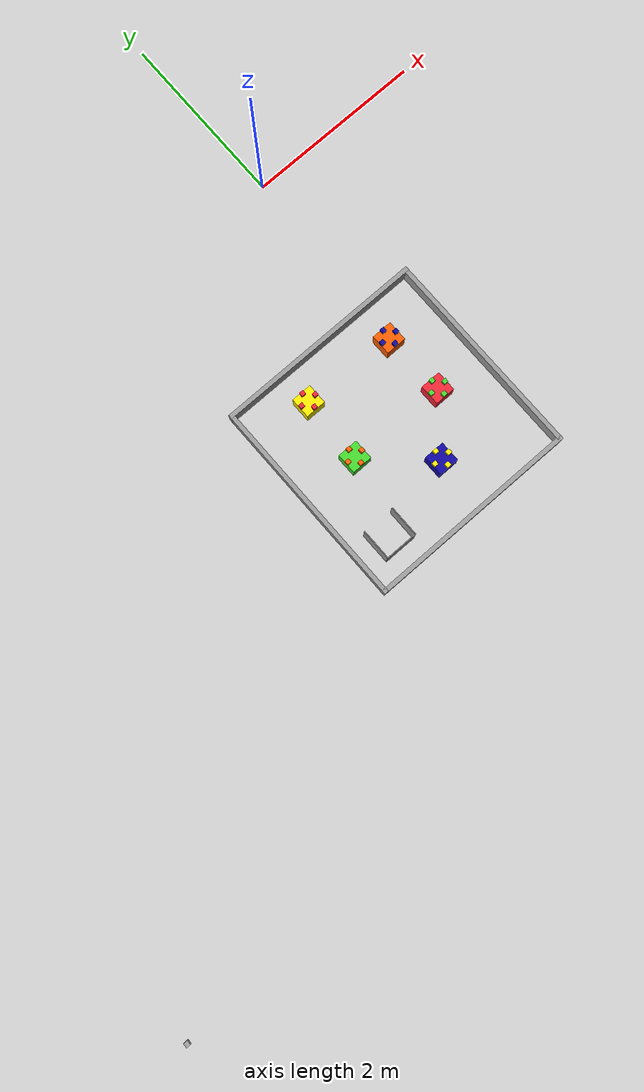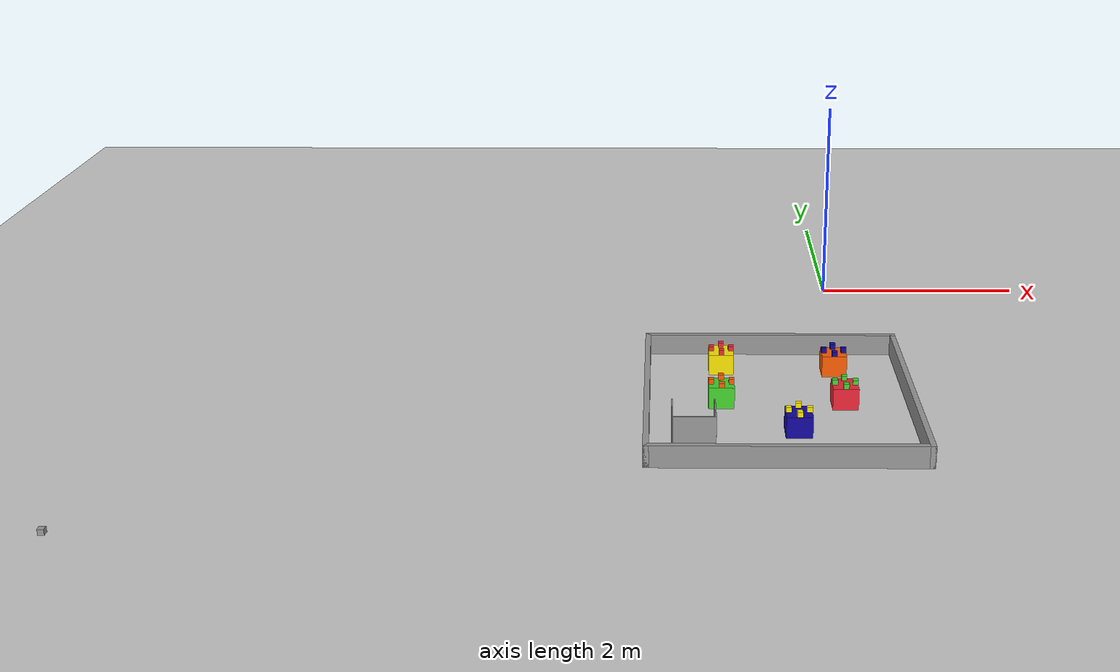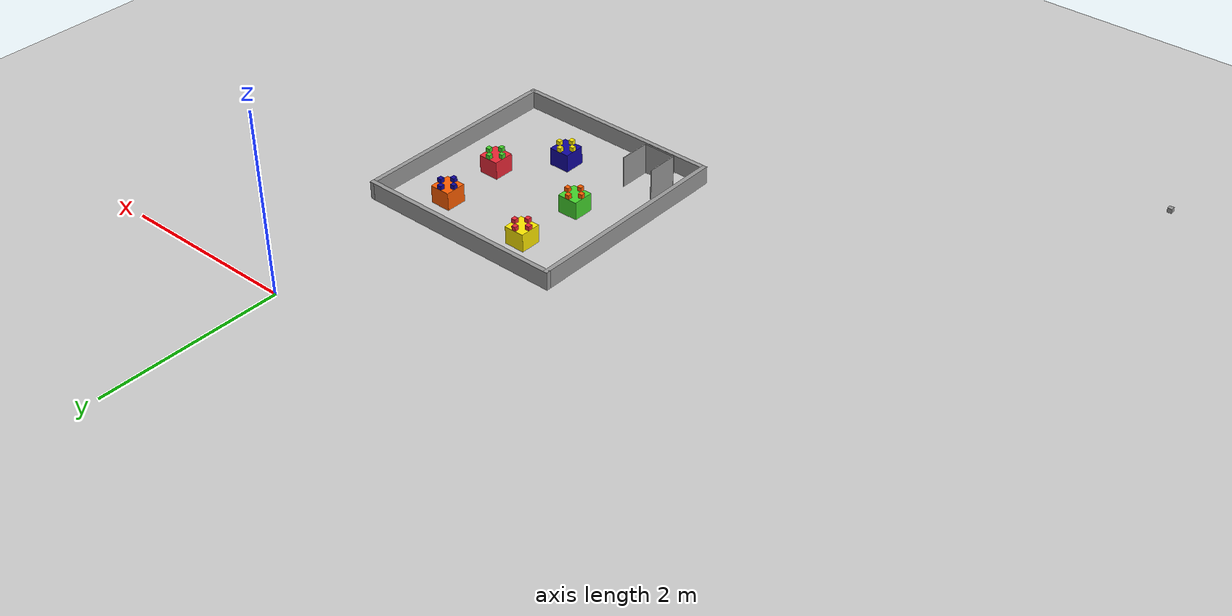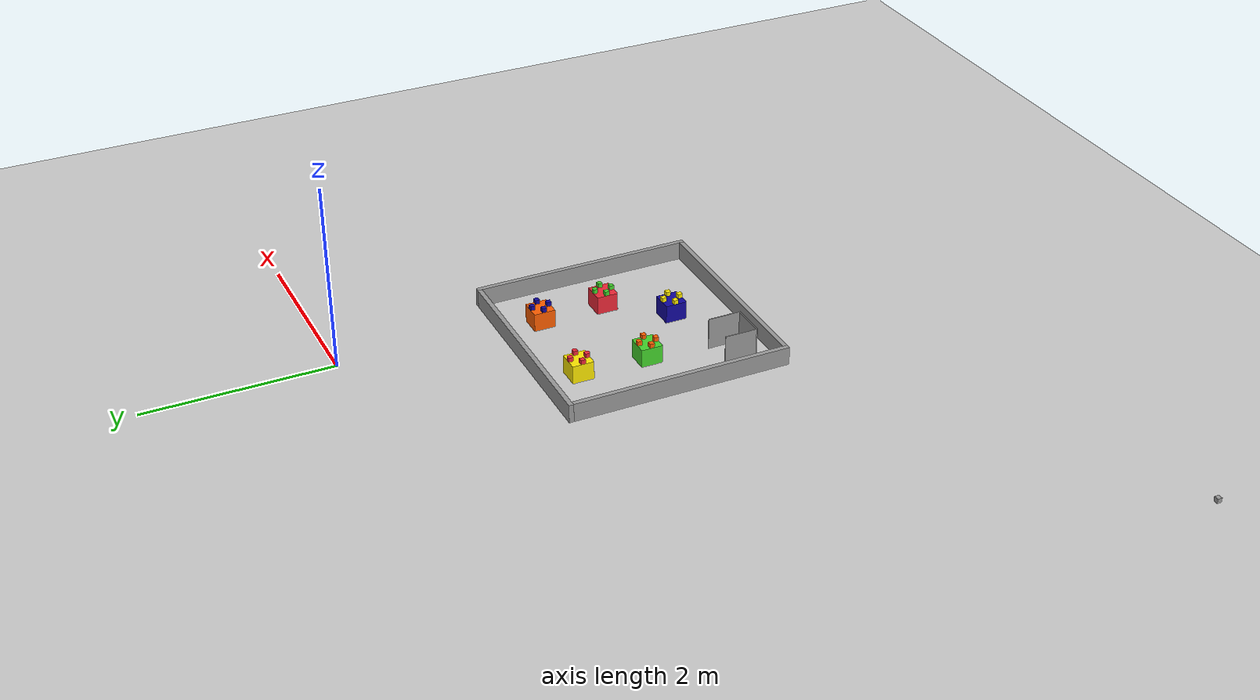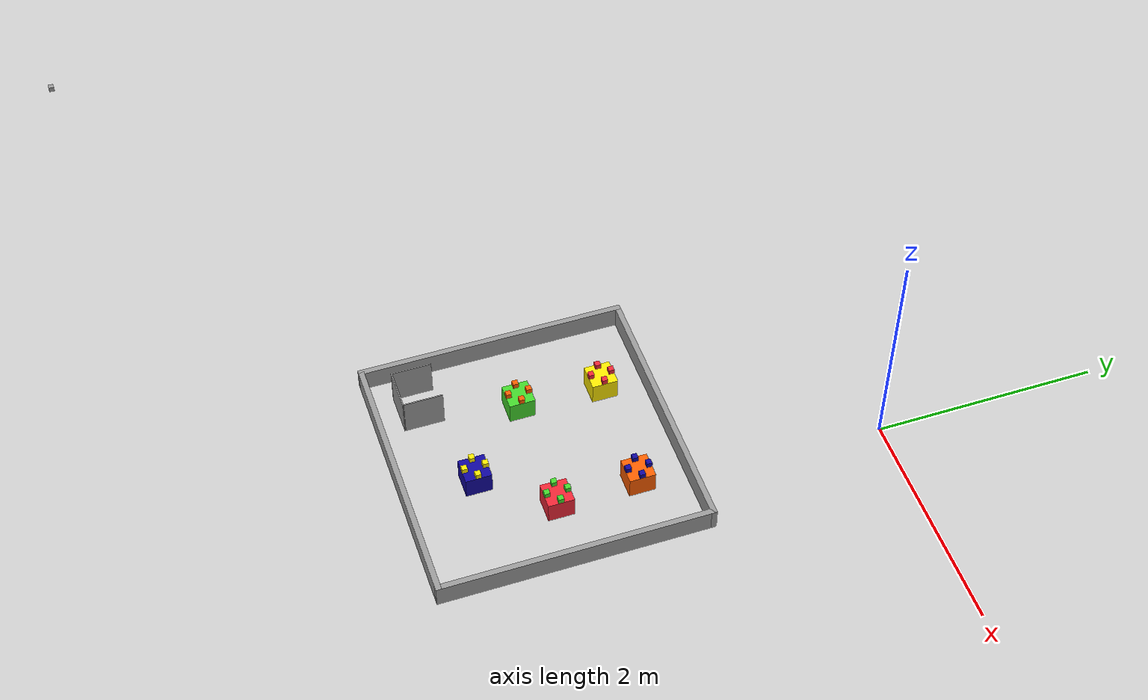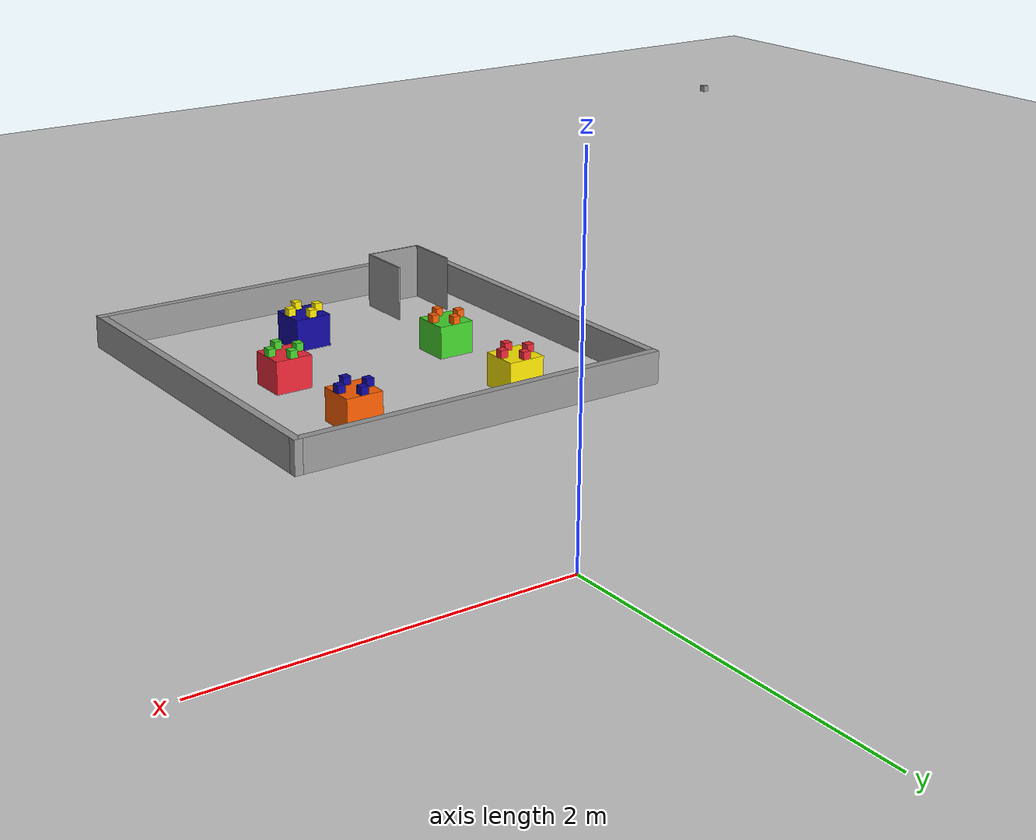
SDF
<sdf version="1.6">
 <world name="default">
  <light name="sun" type="directional">
   <pose>0 0 10 0 -0 0</pose>
   <diffuse>0.8 0.8 0.8 1</diffuse>
   <specular>0.1 0.1 0.1 1</specular>
   <attenuation>
    <range>1000</range>
    <constant>0.9</constant>
    <linear>0.01</linear>
    <quadratic>0.001</quadratic>
   </attenuation>
   <direction>-0.5 0.5 -1</direction>
  </light>
  <model name="ground_plane">
   <static>1</static>
   <link name="link">
    <collision name="collision">
     <geometry><plane><normal>0 0 1</normal><size>100 100</size></plane></geometry>
     <surface><friction><ode><mu>100</mu><mu2>50</mu2></ode></friction></surface>
    </collision>
    <visual name="visual">
     <cast_shadows>0</cast_shadows>
     <geometry><plane><normal>0 0 1</normal><size>100 100</size></plane></geometry>
     <material>
      <script><uri>file://media/materials/scripts/gazebo.material</uri><name>Gazebo/Grey</name></script>
     </material>
    </visual>
   </link>
  </model>
  <gravity>0 0 -9.8</gravity>
  <magnetic_field>6e-06 2.3e-05 -4.2e-05</magnetic_field>
  <atmosphere type="adiabatic"/>
  <physics name="default_physics" default="0" type="ode">
   <max_step_size>0.001</max_step_size>
   <real_time_factor>1</real_time_factor>
   <real_time_update_rate>1000</real_time_update_rate>
  </physics>
  <scene><ambient>0.4 0.4 0.4 1</ambient><background>0.7 0.7 0.7 1</background><shadows>1</shadows></scene>
  <spherical_coordinates>
   <surface_model>EARTH_WGS84</surface_model>
   <latitude_deg>0</latitude_deg>
   <longitude_deg>0</longitude_deg>
   <elevation>0</elevation>
   <heading_deg>0</heading_deg>
  </spherical_coordinates>
  <model name="wro_arc__parking">
   <link name="link_4">
    <pose>0.73944 -0.058801 -0.110769 0 -0 0</pose>
    <inertial>
     <mass>1</mass>
     <inertia>
      <ixx>0.166667</ixx>
      <ixy>0</ixy>
      <ixz>0</ixz>
      <iyy>0.166667</iyy>
      <iyz>0</iyz>
      <izz>0.166667</izz>
     </inertia>
    </inertial>
    <visual name="visual">
     <geometry><box><size>0.23 0.23 0.2</size></box></geometry>
     <material>
      <lighting>1</lighting>
      <script><uri>file://media/materials/scripts/gazebo.material</uri><name>Gazebo/Grey</name></script>
      <ambient>0.933 0.153 0.216 1</ambient>
      <diffuse>0.933 0.153 0.216 1</diffuse>
      <specular>0.933 0.153 0.216 1</specular>
      <emissive>0 0 0 1</emissive>
      <shader type="vertex"><normal_map>__default__</normal_map></shader>
     </material>
    </visual>
    <collision name="collision">
     <geometry><box><size>0.23 0.23 0.2</size></box></geometry>
     <surface>
      <friction>
       <ode><mu>1</mu><mu2>1</mu2><fdir1>0 0 0</fdir1><slip1>0</slip1><slip2>0</slip2></ode>
       <torsional>
        <coefficient>1</coefficient>
        <patch_radius>0</patch_radius>
        <surface_radius>0</surface_radius>
        <use_patch_radius>1</use_patch_radius>
        <ode><slip>0</slip></ode>
       </torsional>
      </friction>
      <bounce><restitution_coefficient>0</restitution_coefficient><threshold>1e+06</threshold></bounce>
      <contact>
       <collide_without_contact>0</collide_without_contact>
       <collide_without_contact_bitmask>1</collide_without_contact_bitmask>
       <collide_bitmask>1</collide_bitmask>
       <ode>
        <soft_cfm>0</soft_cfm>
        <soft_erp>0.2</soft_erp>
        <kp>1e+13</kp>
        <kd>1</kd>
        <max_vel>0.01</max_vel>
        <min_depth>0</min_depth>
       </ode>
       <bullet>
        <split_impulse>1</split_impulse>
        <split_impulse_penetration_threshold>-0.01</split_impulse_penetration_threshold>
        <soft_cfm>0</soft_cfm>
        <soft_erp>0.2</soft_erp>
        <kp>1e+13</kp>
        <kd>1</kd>
       </bullet>
      </contact>
     </surface>
    </collision>
   </link>
   <link name="link_4_clone_0">
    <pose>0.281585 -0.627741 -0.110769 0 -0 0</pose>
    <inertial>
     <mass>1</mass>
     <inertia>
      <ixx>0.166667</ixx>
      <ixy>0</ixy>
      <ixz>0</ixz>
      <iyy>0.166667</iyy>
      <iyz>0</iyz>
      <izz>0.166667</izz>
     </inertia>
    </inertial>
    <visual name="visual">
     <geometry><box><size>0.23 0.23 0.2</size></box></geometry>
     <material>
      <lighting>1</lighting>
      <script><uri>file://media/materials/scripts/gazebo.material</uri><name>Gazebo/Grey</name></script>
      <ambient>0.063 0.024 0.624 1</ambient>
      <diffuse>0.063 0.024 0.624 1</diffuse>
      <specular>0.063 0.024 0.624 1</specular>
      <emissive>0 0 0 1</emissive>
      <shader type="vertex"><normal_map>__default__</normal_map></shader>
     </material>
    </visual>
    <collision name="collision">
     <geometry><box><size>0.23 0.23 0.2</size></box></geometry>
     <surface>
      <friction>
       <ode><mu>1</mu><mu2>1</mu2><fdir1>0 0 0</fdir1><slip1>0</slip1><slip2>0</slip2></ode>
       <torsional>
        <coefficient>1</coefficient>
        <patch_radius>0</patch_radius>
        <surface_radius>0</surface_radius>
        <use_patch_radius>1</use_patch_radius>
        <ode><slip>0</slip></ode>
       </torsional>
      </friction>
      <bounce><restitution_coefficient>0</restitution_coefficient><threshold>1e+06</threshold></bounce>
      <contact>
       <collide_without_contact>0</collide_without_contact>
       <collide_without_contact_bitmask>1</collide_without_contact_bitmask>
       <collide_bitmask>1</collide_bitmask>
       <ode>
        <soft_cfm>0</soft_cfm>
        <soft_erp>0.2</soft_erp>
        <kp>1e+13</kp>
        <kd>1</kd>
        <max_vel>0.01</max_vel>
        <min_depth>0</min_depth>
       </ode>
       <bullet>
        <split_impulse>1</split_impulse>
        <split_impulse_penetration_threshold>-0.01</split_impulse_penetration_threshold>
        <soft_cfm>0</soft_cfm>
        <soft_erp>0.2</soft_erp>
        <kp>1e+13</kp>
        <kd>1</kd>
       </bullet>
      </contact>
     </surface>
    </collision>
   </link>
   <link name="link_4_clone_1">
    <pose>-0.363213 -0.039221 -0.110769 0 -0 0</pose>
    <inertial>
     <mass>1</mass>
     <inertia>
      <ixx>0.166667</ixx>
      <ixy>0</ixy>
      <ixz>0</ixz>
      <iyy>0.166667</iyy>
      <iyz>0</iyz>
      <izz>0.166667</izz>
     </inertia>
    </inertial>
    <visual name="visual">
     <geometry><box><size>0.23 0.23 0.2</size></box></geometry>
     <material>
      <lighting>1</lighting>
      <script><uri>file://media/materials/scripts/gazebo.material</uri><name>Gazebo/Grey</name></script>
      <ambient>0.267 0.839 0.173 1</ambient>
      <diffuse>0.267 0.839 0.173 1</diffuse>
      <specular>0.267 0.839 0.173 1</specular>
      <emissive>0 0 0 1</emissive>
      <shader type="vertex"><normal_map>__default__</normal_map></shader>
     </material>
    </visual>
    <collision name="collision">
     <geometry><box><size>0.23 0.23 0.2</size></box></geometry>
     <surface>
      <friction>
       <ode><mu>1</mu><mu2>1</mu2><fdir1>0 0 0</fdir1><slip1>0</slip1><slip2>0</slip2></ode>
       <torsional>
        <coefficient>1</coefficient>
        <patch_radius>0</patch_radius>
        <surface_radius>0</surface_radius>
        <use_patch_radius>1</use_patch_radius>
        <ode><slip>0</slip></ode>
       </torsional>
      </friction>
      <bounce><restitution_coefficient>0</restitution_coefficient><threshold>1e+06</threshold></bounce>
      <contact>
       <collide_without_contact>0</collide_without_contact>
       <collide_without_contact_bitmask>1</collide_without_contact_bitmask>
       <collide_bitmask>1</collide_bitmask>
       <ode>
        <soft_cfm>0</soft_cfm>
        <soft_erp>0.2</soft_erp>
        <kp>1e+13</kp>
        <kd>1</kd>
        <max_vel>0.01</max_vel>
        <min_depth>0</min_depth>
       </ode>
       <bullet>
        <split_impulse>1</split_impulse>
        <split_impulse_penetration_threshold>-0.01</split_impulse_penetration_threshold>
        <soft_cfm>0</soft_cfm>
        <soft_erp>0.2</soft_erp>
        <kp>1e+13</kp>
        <kd>1</kd>
       </bullet>
      </contact>
     </surface>
    </collision>
   </link>
   <link name="link_4_clone_2">
    <pose>-0.339883 0.701029 -0.110769 0 -0 0</pose>
    <inertial>
     <mass>1</mass>
     <inertia>
      <ixx>0.166667</ixx>
      <ixy>0</ixy>
      <ixz>0</ixz>
      <iyy>0.166667</iyy>
      <iyz>0</iyz>
      <izz>0.166667</izz>
     </inertia>
    </inertial>
    <visual name="visual">
     <geometry><box><size>0.23 0.23 0.2</size></box></geometry>
     <material>
      <lighting>1</lighting>
      <script><uri>file://media/materials/scripts/gazebo.material</uri><name>Gazebo/Grey</name></script>
      <ambient>0.996 0.914 0 1</ambient>
      <diffuse>0.996 0.914 0 1</diffuse>
      <specular>0.996 0.914 0 1</specular>
      <emissive>0 0 0 1</emissive>
      <shader type="vertex"><normal_map>__default__</normal_map></shader>
     </material>
    </visual>
    <collision name="collision">
     <geometry><box><size>0.23 0.23 0.2</size></box></geometry>
     <surface>
      <friction>
       <ode><mu>1</mu><mu2>1</mu2><fdir1>0 0 0</fdir1><slip1>0</slip1><slip2>0</slip2></ode>
       <torsional>
        <coefficient>1</coefficient>
        <patch_radius>0</patch_radius>
        <surface_radius>0</surface_radius>
        <use_patch_radius>1</use_patch_radius>
        <ode><slip>0</slip></ode>
       </torsional>
      </friction>
      <bounce><restitution_coefficient>0</restitution_coefficient><threshold>1e+06</threshold></bounce>
      <contact>
       <collide_without_contact>0</collide_without_contact>
       <collide_without_contact_bitmask>1</collide_without_contact_bitmask>
       <collide_bitmask>1</collide_bitmask>
       <ode>
        <soft_cfm>0</soft_cfm>
        <soft_erp>0.2</soft_erp>
        <kp>1e+13</kp>
        <kd>1</kd>
        <max_vel>0.01</max_vel>
        <min_depth>0</min_depth>
       </ode>
       <bullet>
        <split_impulse>1</split_impulse>
        <split_impulse_penetration_threshold>-0.01</split_impulse_penetration_threshold>
        <soft_cfm>0</soft_cfm>
        <soft_erp>0.2</soft_erp>
        <kp>1e+13</kp>
        <kd>1</kd>
       </bullet>
      </contact>
     </surface>
    </collision>
   </link>
   <link name="link_4_clone_3">
    <pose>0.713356 0.661649 -0.110769 0 -0 0</pose>
    <inertial>
     <mass>1</mass>
     <inertia>
      <ixx>0.166667</ixx>
      <ixy>0</ixy>
      <ixz>0</ixz>
      <iyy>0.166667</iyy>
      <iyz>0</iyz>
      <izz>0.166667</izz>
     </inertia>
    </inertial>
    <visual name="visual">
     <geometry><box><size>0.23 0.23 0.2</size></box></geometry>
     <material>
      <lighting>1</lighting>
      <script><uri>file://media/materials/scripts/gazebo.material</uri><name>Gazebo/Grey</name></script>
      <ambient>0.996 0.368 0 1</ambient>
      <diffuse>0.996 0.368 0 1</diffuse>
      <specular>0.996 0.368 0 1</specular>
      <emissive>0 0 0 1</emissive>
      <shader type="vertex"><normal_map>__default__</normal_map></shader>
     </material>
    </visual>
    <collision name="collision">
     <geometry><box><size>0.23 0.23 0.2</size></box></geometry>
     <surface>
      <friction>
       <ode><mu>1</mu><mu2>1</mu2><fdir1>0 0 0</fdir1><slip1>0</slip1><slip2>0</slip2></ode>
       <torsional>
        <coefficient>1</coefficient>
        <patch_radius>0</patch_radius>
        <surface_radius>0</surface_radius>
        <use_patch_radius>1</use_patch_radius>
        <ode><slip>0</slip></ode>
       </torsional>
      </friction>
      <bounce><restitution_coefficient>0</restitution_coefficient><threshold>1e+06</threshold></bounce>
      <contact>
       <collide_without_contact>0</collide_without_contact>
       <collide_without_contact_bitmask>1</collide_without_contact_bitmask>
       <collide_bitmask>1</collide_bitmask>
       <ode>
        <soft_cfm>0</soft_cfm>
        <soft_erp>0.2</soft_erp>
        <kp>1e+13</kp>
        <kd>1</kd>
        <max_vel>0.01</max_vel>
        <min_depth>0</min_depth>
       </ode>
       <bullet>
        <split_impulse>1</split_impulse>
        <split_impulse_penetration_threshold>-0.01</split_impulse_penetration_threshold>
        <soft_cfm>0</soft_cfm>
        <soft_erp>0.2</soft_erp>
        <kp>1e+13</kp>
        <kd>1</kd>
       </bullet>
      </contact>
     </surface>
    </collision>
   </link>
   <link name="link_5">
    <pose>-5.15643 -3.18462 0.289231 0 -0 0</pose>
    <inertial>
     <mass>1</mass>
     <inertia>
      <ixx>0.166667</ixx>
      <ixy>0</ixy>
      <ixz>0</ixz>
      <iyy>0.166667</iyy>
      <iyz>0</iyz>
      <izz>0.166667</izz>
     </inertia>
    </inertial>
    <visual name="visual">
     <geometry><box><size>0.048 0.048 0.048</size></box></geometry>
     <material>
      <lighting>1</lighting>
      <script><uri>file://media/materials/scripts/gazebo.material</uri><name>Gazebo/Grey</name></script>
      <ambient>0.3 0.3 0.3 1</ambient>
      <diffuse>0.7 0.7 0.7 1</diffuse>
      <specular>0.01 0.01 0.01 1</specular>
      <emissive>0 0 0 1</emissive>
      <shader type="vertex"><normal_map>__default__</normal_map></shader>
     </material>
    </visual>
    <collision name="collision">
     <geometry><box><size>0.048 0.048 0.048</size></box></geometry>
     <surface>
      <friction>
       <ode><mu>1</mu><mu2>1</mu2><fdir1>0 0 0</fdir1><slip1>0</slip1><slip2>0</slip2></ode>
       <torsional>
        <coefficient>1</coefficient>
        <patch_radius>0</patch_radius>
        <surface_radius>0</surface_radius>
        <use_patch_radius>1</use_patch_radius>
        <ode><slip>0</slip></ode>
       </torsional>
      </friction>
      <bounce><restitution_coefficient>0</restitution_coefficient><threshold>1e+06</threshold></bounce>
      <contact>
       <collide_without_contact>0</collide_without_contact>
       <collide_without_contact_bitmask>1</collide_without_contact_bitmask>
       <collide_bitmask>1</collide_bitmask>
       <ode>
        <soft_cfm>0</soft_cfm>
        <soft_erp>0.2</soft_erp>
        <kp>1e+13</kp>
        <kd>1</kd>
        <max_vel>0.01</max_vel>
        <min_depth>0</min_depth>
       </ode>
       <bullet>
        <split_impulse>1</split_impulse>
        <split_impulse_penetration_threshold>-0.01</split_impulse_penetration_threshold>
        <soft_cfm>0</soft_cfm>
        <soft_erp>0.2</soft_erp>
        <kp>1e+13</kp>
        <kd>1</kd>
       </bullet>
      </contact>
     </surface>
    </collision>
   </link>
   <link name="link_5_clone">
    <pose>0.83044 -0.058801 0.013231 0 -0 0</pose>
    <inertial>
     <mass>1</mass>
     <inertia>
      <ixx>0.166667</ixx>
      <ixy>0</ixy>
      <ixz>0</ixz>
      <iyy>0.166667</iyy>
      <iyz>0</iyz>
      <izz>0.166667</izz>
     </inertia>
    </inertial>
    <visual name="visual">
     <geometry><box><size>0.048 0.048 0.048</size></box></geometry>
     <material>
      <lighting>1</lighting>
      <script><uri>file://media/materials/scripts/gazebo.material</uri><name>Gazebo/Grey</name></script>
      <ambient>0.267 0.839 0.173 1</ambient>
      <diffuse>0.267 0.839 0.173 1</diffuse>
      <specular>0.267 0.839 0.173 1</specular>
      <emissive>0 0 0 1</emissive>
      <shader type="vertex"><normal_map>__default__</normal_map></shader>
     </material>
    </visual>
    <collision name="collision">
     <geometry><box><size>0.048 0.048 0.048</size></box></geometry>
     <surface>
      <friction>
       <ode><mu>1</mu><mu2>1</mu2><fdir1>0 0 0</fdir1><slip1>0</slip1><slip2>0</slip2></ode>
       <torsional>
        <coefficient>1</coefficient>
        <patch_radius>0</patch_radius>
        <surface_radius>0</surface_radius>
        <use_patch_radius>1</use_patch_radius>
        <ode><slip>0</slip></ode>
       </torsional>
      </friction>
      <bounce><restitution_coefficient>0</restitution_coefficient><threshold>1e+06</threshold></bounce>
      <contact>
       <collide_without_contact>0</collide_without_contact>
       <collide_without_contact_bitmask>1</collide_without_contact_bitmask>
       <collide_bitmask>1</collide_bitmask>
       <ode>
        <soft_cfm>0</soft_cfm>
        <soft_erp>0.2</soft_erp>
        <kp>1e+13</kp>
        <kd>1</kd>
        <max_vel>0.01</max_vel>
        <min_depth>0</min_depth>
       </ode>
       <bullet>
        <split_impulse>1</split_impulse>
        <split_impulse_penetration_threshold>-0.01</split_impulse_penetration_threshold>
        <soft_cfm>0</soft_cfm>
        <soft_erp>0.2</soft_erp>
        <kp>1e+13</kp>
        <kd>1</kd>
       </bullet>
      </contact>
     </surface>
    </collision>
   </link>
   <link name="link_5_clone_0">
    <pose>0.64844 -0.058781 0.013231 0 -0 0</pose>
    <inertial>
     <mass>1</mass>
     <inertia>
      <ixx>0.166667</ixx>
      <ixy>0</ixy>
      <ixz>0</ixz>
      <iyy>0.166667</iyy>
      <iyz>0</iyz>
      <izz>0.166667</izz>
     </inertia>
    </inertial>
    <visual name="visual">
     <geometry><box><size>0.048 0.048 0.048</size></box></geometry>
     <material>
      <lighting>1</lighting>
      <script><uri>file://media/materials/scripts/gazebo.material</uri><name>Gazebo/Grey</name></script>
      <ambient>0.267 0.839 0.173 1</ambient>
      <diffuse>0.267 0.839 0.173 1</diffuse>
      <specular>0.267 0.839 0.173 1</specular>
      <emissive>0 0 0 1</emissive>
      <shader type="vertex"><normal_map>__default__</normal_map></shader>
     </material>
    </visual>
    <collision name="collision">
     <geometry><box><size>0.048 0.048 0.048</size></box></geometry>
     <surface>
      <friction>
       <ode><mu>1</mu><mu2>1</mu2><fdir1>0 0 0</fdir1><slip1>0</slip1><slip2>0</slip2></ode>
       <torsional>
        <coefficient>1</coefficient>
        <patch_radius>0</patch_radius>
        <surface_radius>0</surface_radius>
        <use_patch_radius>1</use_patch_radius>
        <ode><slip>0</slip></ode>
       </torsional>
      </friction>
      <bounce><restitution_coefficient>0</restitution_coefficient><threshold>1e+06</threshold></bounce>
      <contact>
       <collide_without_contact>0</collide_without_contact>
       <collide_without_contact_bitmask>1</collide_without_contact_bitmask>
       <collide_bitmask>1</collide_bitmask>
       <ode>
        <soft_cfm>0</soft_cfm>
        <soft_erp>0.2</soft_erp>
        <kp>1e+13</kp>
        <kd>1</kd>
        <max_vel>0.01</max_vel>
        <min_depth>0</min_depth>
       </ode>
       <bullet>
        <split_impulse>1</split_impulse>
        <split_impulse_penetration_threshold>-0.01</split_impulse_penetration_threshold>
        <soft_cfm>0</soft_cfm>
        <soft_erp>0.2</soft_erp>
        <kp>1e+13</kp>
        <kd>1</kd>
       </bullet>
      </contact>
     </surface>
    </collision>
   </link>
   <link name="link_5_clone_1">
    <pose>0.73944 0.032199 0.013231 0 -0 0</pose>
    <inertial>
     <mass>1</mass>
     <inertia>
      <ixx>0.166667</ixx>
      <ixy>0</ixy>
      <ixz>0</ixz>
      <iyy>0.166667</iyy>
      <iyz>0</iyz>
      <izz>0.166667</izz>
     </inertia>
    </inertial>
    <visual name="visual">
     <geometry><box><size>0.048 0.048 0.048</size></box></geometry>
     <material>
      <lighting>1</lighting>
      <script><uri>file://media/materials/scripts/gazebo.material</uri><name>Gazebo/Grey</name></script>
      <ambient>0.267 0.839 0.173 1</ambient>
      <diffuse>0.267 0.839 0.173 1</diffuse>
      <specular>0.267 0.839 0.173 1</specular>
      <emissive>0 0 0 1</emissive>
      <shader type="vertex"><normal_map>__default__</normal_map></shader>
     </material>
    </visual>
    <collision name="collision">
     <geometry><box><size>0.048 0.048 0.048</size></box></geometry>
     <surface>
      <friction>
       <ode><mu>1</mu><mu2>1</mu2><fdir1>0 0 0</fdir1><slip1>0</slip1><slip2>0</slip2></ode>
       <torsional>
        <coefficient>1</coefficient>
        <patch_radius>0</patch_radius>
        <surface_radius>0</surface_radius>
        <use_patch_radius>1</use_patch_radius>
        <ode><slip>0</slip></ode>
       </torsional>
      </friction>
      <bounce><restitution_coefficient>0</restitution_coefficient><threshold>1e+06</threshold></bounce>
      <contact>
       <collide_without_contact>0</collide_without_contact>
       <collide_without_contact_bitmask>1</collide_without_contact_bitmask>
       <collide_bitmask>1</collide_bitmask>
       <ode>
        <soft_cfm>0</soft_cfm>
        <soft_erp>0.2</soft_erp>
        <kp>1e+13</kp>
        <kd>1</kd>
        <max_vel>0.01</max_vel>
        <min_depth>0</min_depth>
       </ode>
       <bullet>
        <split_impulse>1</split_impulse>
        <split_impulse_penetration_threshold>-0.01</split_impulse_penetration_threshold>
        <soft_cfm>0</soft_cfm>
        <soft_erp>0.2</soft_erp>
        <kp>1e+13</kp>
        <kd>1</kd>
       </bullet>
      </contact>
     </surface>
    </collision>
   </link>
   <link name="link_5_clone_clone">
    <pose>0.73944 -0.149801 0.013231 0 -0 0</pose>
    <inertial>
     <mass>1</mass>
     <inertia>
      <ixx>0.166667</ixx>
      <ixy>0</ixy>
      <ixz>0</ixz>
      <iyy>0.166667</iyy>
      <iyz>0</iyz>
      <izz>0.166667</izz>
     </inertia>
    </inertial>
    <visual name="visual">
     <geometry><box><size>0.048 0.048 0.048</size></box></geometry>
     <material>
      <lighting>1</lighting>
      <script><uri>file://media/materials/scripts/gazebo.material</uri><name>Gazebo/Grey</name></script>
      <ambient>0.267 0.839 0.173 1</ambient>
      <diffuse>0.267 0.839 0.173 1</diffuse>
      <specular>0.267 0.839 0.173 1</specular>
      <emissive>0 0 0 1</emissive>
      <shader type="vertex"><normal_map>__default__</normal_map></shader>
     </material>
    </visual>
    <collision name="collision">
     <geometry><box><size>0.048 0.048 0.048</size></box></geometry>
     <surface>
      <friction>
       <ode><mu>1</mu><mu2>1</mu2><fdir1>0 0 0</fdir1><slip1>0</slip1><slip2>0</slip2></ode>
       <torsional>
        <coefficient>1</coefficient>
        <patch_radius>0</patch_radius>
        <surface_radius>0</surface_radius>
        <use_patch_radius>1</use_patch_radius>
        <ode><slip>0</slip></ode>
       </torsional>
      </friction>
      <bounce><restitution_coefficient>0</restitution_coefficient><threshold>1e+06</threshold></bounce>
      <contact>
       <collide_without_contact>0</collide_without_contact>
       <collide_without_contact_bitmask>1</collide_without_contact_bitmask>
       <collide_bitmask>1</collide_bitmask>
       <ode>
        <soft_cfm>0</soft_cfm>
        <soft_erp>0.2</soft_erp>
        <kp>1e+13</kp>
        <kd>1</kd>
        <max_vel>0.01</max_vel>
        <min_depth>0</min_depth>
       </ode>
       <bullet>
        <split_impulse>1</split_impulse>
        <split_impulse_penetration_threshold>-0.01</split_impulse_penetration_threshold>
        <soft_cfm>0</soft_cfm>
        <soft_erp>0.2</soft_erp>
        <kp>1e+13</kp>
        <kd>1</kd>
       </bullet>
      </contact>
     </surface>
    </collision>
   </link>
   <link name="link_5_clone_clone_clone">
    <pose>0.281585 -0.536741 0.013231 0 -0 0</pose>
    <inertial>
     <mass>1</mass>
     <inertia>
      <ixx>0.166667</ixx>
      <ixy>0</ixy>
      <ixz>0</ixz>
      <iyy>0.166667</iyy>
      <iyz>0</iyz>
      <izz>0.166667</izz>
     </inertia>
    </inertial>
    <visual name="visual">
     <geometry><box><size>0.048 0.048 0.048</size></box></geometry>
     <material>
      <lighting>1</lighting>
      <script><uri>file://media/materials/scripts/gazebo.material</uri><name>Gazebo/Grey</name></script>
      <ambient>0.996 0.914 0 1</ambient>
      <diffuse>0.996 0.914 0 1</diffuse>
      <specular>0.996 0.914 0 1</specular>
      <emissive>0 0 0 1</emissive>
      <shader type="vertex"><normal_map>__default__</normal_map></shader>
     </material>
    </visual>
    <collision name="collision">
     <geometry><box><size>0.048 0.048 0.048</size></box></geometry>
     <surface>
      <friction>
       <ode><mu>1</mu><mu2>1</mu2><fdir1>0 0 0</fdir1><slip1>0</slip1><slip2>0</slip2></ode>
       <torsional>
        <coefficient>1</coefficient>
        <patch_radius>0</patch_radius>
        <surface_radius>0</surface_radius>
        <use_patch_radius>1</use_patch_radius>
        <ode><slip>0</slip></ode>
       </torsional>
      </friction>
      <bounce><restitution_coefficient>0</restitution_coefficient><threshold>1e+06</threshold></bounce>
      <contact>
       <collide_without_contact>0</collide_without_contact>
       <collide_without_contact_bitmask>1</collide_without_contact_bitmask>
       <collide_bitmask>1</collide_bitmask>
       <ode>
        <soft_cfm>0</soft_cfm>
        <soft_erp>0.2</soft_erp>
        <kp>1e+13</kp>
        <kd>1</kd>
        <max_vel>0.01</max_vel>
        <min_depth>0</min_depth>
       </ode>
       <bullet>
        <split_impulse>1</split_impulse>
        <split_impulse_penetration_threshold>-0.01</split_impulse_penetration_threshold>
        <soft_cfm>0</soft_cfm>
        <soft_erp>0.2</soft_erp>
        <kp>1e+13</kp>
        <kd>1</kd>
       </bullet>
      </contact>
     </surface>
    </collision>
   </link>
   <link name="link_5_clone_clone_clone_0">
    <pose>0.281585 -0.718741 0.013231 0 -0 0</pose>
    <inertial>
     <mass>1</mass>
     <inertia>
      <ixx>0.166667</ixx>
      <ixy>0</ixy>
      <ixz>0</ixz>
      <iyy>0.166667</iyy>
      <iyz>0</iyz>
      <izz>0.166667</izz>
     </inertia>
    </inertial>
    <visual name="visual">
     <geometry><box><size>0.048 0.048 0.048</size></box></geometry>
     <material>
      <lighting>1</lighting>
      <script><uri>file://media/materials/scripts/gazebo.material</uri><name>Gazebo/Grey</name></script>
      <ambient>0.996 0.914 0 1</ambient>
      <diffuse>0.996 0.914 0 1</diffuse>
      <specular>0.996 0.914 0 1</specular>
      <emissive>0 0 0 1</emissive>
      <shader type="vertex"><normal_map>__default__</normal_map></shader>
     </material>
    </visual>
    <collision name="collision">
     <geometry><box><size>0.048 0.048 0.048</size></box></geometry>
     <surface>
      <friction>
       <ode><mu>1</mu><mu2>1</mu2><fdir1>0 0 0</fdir1><slip1>0</slip1><slip2>0</slip2></ode>
       <torsional>
        <coefficient>1</coefficient>
        <patch_radius>0</patch_radius>
        <surface_radius>0</surface_radius>
        <use_patch_radius>1</use_patch_radius>
        <ode><slip>0</slip></ode>
       </torsional>
      </friction>
      <bounce><restitution_coefficient>0</restitution_coefficient><threshold>1e+06</threshold></bounce>
      <contact>
       <collide_without_contact>0</collide_without_contact>
       <collide_without_contact_bitmask>1</collide_without_contact_bitmask>
       <collide_bitmask>1</collide_bitmask>
       <ode>
        <soft_cfm>0</soft_cfm>
        <soft_erp>0.2</soft_erp>
        <kp>1e+13</kp>
        <kd>1</kd>
        <max_vel>0.01</max_vel>
        <min_depth>0</min_depth>
       </ode>
       <bullet>
        <split_impulse>1</split_impulse>
        <split_impulse_penetration_threshold>-0.01</split_impulse_penetration_threshold>
        <soft_cfm>0</soft_cfm>
        <soft_erp>0.2</soft_erp>
        <kp>1e+13</kp>
        <kd>1</kd>
       </bullet>
      </contact>
     </surface>
    </collision>
   </link>
   <link name="link_5_clone_clone_clone_1">
    <pose>0.190585 -0.627741 0.013231 0 -0 0</pose>
    <inertial>
     <mass>1</mass>
     <inertia>
      <ixx>0.166667</ixx>
      <ixy>0</ixy>
      <ixz>0</ixz>
      <iyy>0.166667</iyy>
      <iyz>0</iyz>
      <izz>0.166667</izz>
     </inertia>
    </inertial>
    <visual name="visual">
     <geometry><box><size>0.048 0.048 0.048</size></box></geometry>
     <material>
      <lighting>1</lighting>
      <script><uri>file://media/materials/scripts/gazebo.material</uri><name>Gazebo/Grey</name></script>
      <ambient>0.996 0.914 0 1</ambient>
      <diffuse>0.996 0.914 0 1</diffuse>
      <specular>0.996 0.914 0 1</specular>
      <emissive>0 0 0 1</emissive>
      <shader type="vertex"><normal_map>__default__</normal_map></shader>
     </material>
    </visual>
    <collision name="collision">
     <geometry><box><size>0.048 0.048 0.048</size></box></geometry>
     <surface>
      <friction>
       <ode><mu>1</mu><mu2>1</mu2><fdir1>0 0 0</fdir1><slip1>0</slip1><slip2>0</slip2></ode>
       <torsional>
        <coefficient>1</coefficient>
        <patch_radius>0</patch_radius>
        <surface_radius>0</surface_radius>
        <use_patch_radius>1</use_patch_radius>
        <ode><slip>0</slip></ode>
       </torsional>
      </friction>
      <bounce><restitution_coefficient>0</restitution_coefficient><threshold>1e+06</threshold></bounce>
      <contact>
       <collide_without_contact>0</collide_without_contact>
       <collide_without_contact_bitmask>1</collide_without_contact_bitmask>
       <collide_bitmask>1</collide_bitmask>
       <ode>
        <soft_cfm>0</soft_cfm>
        <soft_erp>0.2</soft_erp>
        <kp>1e+13</kp>
        <kd>1</kd>
        <max_vel>0.01</max_vel>
        <min_depth>0</min_depth>
       </ode>
       <bullet>
        <split_impulse>1</split_impulse>
        <split_impulse_penetration_threshold>-0.01</split_impulse_penetration_threshold>
        <soft_cfm>0</soft_cfm>
        <soft_erp>0.2</soft_erp>
        <kp>1e+13</kp>
        <kd>1</kd>
       </bullet>
      </contact>
     </surface>
    </collision>
   </link>
   <link name="link_5_clone_clone_clone_2">
    <pose>0.372585 -0.627741 0.013231 0 -0 0</pose>
    <inertial>
     <mass>1</mass>
     <inertia>
      <ixx>0.166667</ixx>
      <ixy>0</ixy>
      <ixz>0</ixz>
      <iyy>0.166667</iyy>
      <iyz>0</iyz>
      <izz>0.166667</izz>
     </inertia>
    </inertial>
    <visual name="visual">
     <geometry><box><size>0.048 0.048 0.048</size></box></geometry>
     <material>
      <lighting>1</lighting>
      <script><uri>file://media/materials/scripts/gazebo.material</uri><name>Gazebo/Grey</name></script>
      <ambient>0.996 0.914 0 1</ambient>
      <diffuse>0.996 0.914 0 1</diffuse>
      <specular>0.996 0.914 0 1</specular>
      <emissive>0 0 0 1</emissive>
      <shader type="vertex"><normal_map>__default__</normal_map></shader>
     </material>
    </visual>
    <collision name="collision">
     <geometry><box><size>0.048 0.048 0.048</size></box></geometry>
     <surface>
      <friction>
       <ode><mu>1</mu><mu2>1</mu2><fdir1>0 0 0</fdir1><slip1>0</slip1><slip2>0</slip2></ode>
       <torsional>
        <coefficient>1</coefficient>
        <patch_radius>0</patch_radius>
        <surface_radius>0</surface_radius>
        <use_patch_radius>1</use_patch_radius>
        <ode><slip>0</slip></ode>
       </torsional>
      </friction>
      <bounce><restitution_coefficient>0</restitution_coefficient><threshold>1e+06</threshold></bounce>
      <contact>
       <collide_without_contact>0</collide_without_contact>
       <collide_without_contact_bitmask>1</collide_without_contact_bitmask>
       <collide_bitmask>1</collide_bitmask>
       <ode>
        <soft_cfm>0</soft_cfm>
        <soft_erp>0.2</soft_erp>
        <kp>1e+13</kp>
        <kd>1</kd>
        <max_vel>0.01</max_vel>
        <min_depth>0</min_depth>
       </ode>
       <bullet>
        <split_impulse>1</split_impulse>
        <split_impulse_penetration_threshold>-0.01</split_impulse_penetration_threshold>
        <soft_cfm>0</soft_cfm>
        <soft_erp>0.2</soft_erp>
        <kp>1e+13</kp>
        <kd>1</kd>
       </bullet>
      </contact>
     </surface>
    </collision>
   </link>
   <link name="link_5_clone_clone_clone_clone_clone">
    <pose>-0.363213 -0.130221 0.013231 0 -0 0</pose>
    <inertial>
     <mass>1</mass>
     <inertia>
      <ixx>0.166667</ixx>
      <ixy>0</ixy>
      <ixz>0</ixz>
      <iyy>0.166667</iyy>
      <iyz>0</iyz>
      <izz>0.166667</izz>
     </inertia>
    </inertial>
    <visual name="visual">
     <geometry><box><size>0.048 0.048 0.048</size></box></geometry>
     <material>
      <lighting>1</lighting>
      <script><uri>file://media/materials/scripts/gazebo.material</uri><name>Gazebo/Grey</name></script>
      <ambient>0.996 0.369 0 1</ambient>
      <diffuse>0.996 0.369 0 1</diffuse>
      <specular>0.996 0.369 0 1</specular>
      <emissive>0 0 0 1</emissive>
      <shader type="vertex"><normal_map>__default__</normal_map></shader>
     </material>
    </visual>
    <collision name="collision">
     <geometry><box><size>0.048 0.048 0.048</size></box></geometry>
     <surface>
      <friction>
       <ode><mu>1</mu><mu2>1</mu2><fdir1>0 0 0</fdir1><slip1>0</slip1><slip2>0</slip2></ode>
       <torsional>
        <coefficient>1</coefficient>
        <patch_radius>0</patch_radius>
        <surface_radius>0</surface_radius>
        <use_patch_radius>1</use_patch_radius>
        <ode><slip>0</slip></ode>
       </torsional>
      </friction>
      <bounce><restitution_coefficient>0</restitution_coefficient><threshold>1e+06</threshold></bounce>
      <contact>
       <collide_without_contact>0</collide_without_contact>
       <collide_without_contact_bitmask>1</collide_without_contact_bitmask>
       <collide_bitmask>1</collide_bitmask>
       <ode>
        <soft_cfm>0</soft_cfm>
        <soft_erp>0.2</soft_erp>
        <kp>1e+13</kp>
        <kd>1</kd>
        <max_vel>0.01</max_vel>
        <min_depth>0</min_depth>
       </ode>
       <bullet>
        <split_impulse>1</split_impulse>
        <split_impulse_penetration_threshold>-0.01</split_impulse_penetration_threshold>
        <soft_cfm>0</soft_cfm>
        <soft_erp>0.2</soft_erp>
        <kp>1e+13</kp>
        <kd>1</kd>
       </bullet>
      </contact>
     </surface>
    </collision>
   </link>
   <link name="link_5_clone_clone_clone_clone_clone_0">
    <pose>0.713356 0.570649 0.013231 0 -0 0</pose>
    <inertial>
     <mass>1</mass>
     <inertia>
      <ixx>0.166667</ixx>
      <ixy>0</ixy>
      <ixz>0</ixz>
      <iyy>0.166667</iyy>
      <iyz>0</iyz>
      <izz>0.166667</izz>
     </inertia>
    </inertial>
    <visual name="visual">
     <geometry><box><size>0.048 0.048 0.048</size></box></geometry>
     <material>
      <lighting>1</lighting>
      <script><uri>file://media/materials/scripts/gazebo.material</uri><name>Gazebo/Grey</name></script>
      <ambient>0.063 0.024 0.624 1</ambient>
      <diffuse>0.063 0.024 0.624 1</diffuse>
      <specular>0.063 0.024 0.624 1</specular>
      <emissive>0 0 0 1</emissive>
      <shader type="vertex"><normal_map>__default__</normal_map></shader>
     </material>
    </visual>
    <collision name="collision">
     <geometry><box><size>0.048 0.048 0.048</size></box></geometry>
     <surface>
      <friction>
       <ode><mu>1</mu><mu2>1</mu2><fdir1>0 0 0</fdir1><slip1>0</slip1><slip2>0</slip2></ode>
       <torsional>
        <coefficient>1</coefficient>
        <patch_radius>0</patch_radius>
        <surface_radius>0</surface_radius>
        <use_patch_radius>1</use_patch_radius>
        <ode><slip>0</slip></ode>
       </torsional>
      </friction>
      <bounce><restitution_coefficient>0</restitution_coefficient><threshold>1e+06</threshold></bounce>
      <contact>
       <collide_without_contact>0</collide_without_contact>
       <collide_without_contact_bitmask>1</collide_without_contact_bitmask>
       <collide_bitmask>1</collide_bitmask>
       <ode>
        <soft_cfm>0</soft_cfm>
        <soft_erp>0.2</soft_erp>
        <kp>1e+13</kp>
        <kd>1</kd>
        <max_vel>0.01</max_vel>
        <min_depth>0</min_depth>
       </ode>
       <bullet>
        <split_impulse>1</split_impulse>
        <split_impulse_penetration_threshold>-0.01</split_impulse_penetration_threshold>
        <soft_cfm>0</soft_cfm>
        <soft_erp>0.2</soft_erp>
        <kp>1e+13</kp>
        <kd>1</kd>
       </bullet>
      </contact>
     </surface>
    </collision>
   </link>
   <link name="link_5_clone_clone_clone_clone_clone_0_clone">
    <pose>-0.430883 0.701029 0.013231 0 -0 0</pose>
    <inertial>
     <mass>1</mass>
     <inertia>
      <ixx>0.166667</ixx>
      <ixy>0</ixy>
      <ixz>0</ixz>
      <iyy>0.166667</iyy>
      <iyz>0</iyz>
      <izz>0.166667</izz>
     </inertia>
    </inertial>
    <visual name="visual">
     <geometry><box><size>0.048 0.048 0.048</size></box></geometry>
     <material>
      <lighting>1</lighting>
      <script><uri>file://media/materials/scripts/gazebo.material</uri><name>Gazebo/Grey</name></script>
      <ambient>0.933 0.153 0.216 1</ambient>
      <diffuse>0.933 0.153 0.216 1</diffuse>
      <specular>0.933 0.153 0.216 1</specular>
      <emissive>0 0 0 1</emissive>
      <shader type="vertex"><normal_map>__default__</normal_map></shader>
     </material>
    </visual>
    <collision name="collision">
     <geometry><box><size>0.048 0.048 0.048</size></box></geometry>
     <surface>
      <friction>
       <ode><mu>1</mu><mu2>1</mu2><fdir1>0 0 0</fdir1><slip1>0</slip1><slip2>0</slip2></ode>
       <torsional>
        <coefficient>1</coefficient>
        <patch_radius>0</patch_radius>
        <surface_radius>0</surface_radius>
        <use_patch_radius>1</use_patch_radius>
        <ode><slip>0</slip></ode>
       </torsional>
      </friction>
      <bounce><restitution_coefficient>0</restitution_coefficient><threshold>1e+06</threshold></bounce>
      <contact>
       <collide_without_contact>0</collide_without_contact>
       <collide_without_contact_bitmask>1</collide_without_contact_bitmask>
       <collide_bitmask>1</collide_bitmask>
       <ode>
        <soft_cfm>0</soft_cfm>
        <soft_erp>0.2</soft_erp>
        <kp>1e+13</kp>
        <kd>1</kd>
        <max_vel>0.01</max_vel>
        <min_depth>0</min_depth>
       </ode>
       <bullet>
        <split_impulse>1</split_impulse>
        <split_impulse_penetration_threshold>-0.01</split_impulse_penetration_threshold>
        <soft_cfm>0</soft_cfm>
        <soft_erp>0.2</soft_erp>
        <kp>1e+13</kp>
        <kd>1</kd>
       </bullet>
      </contact>
     </surface>
    </collision>
   </link>
   <link name="link_5_clone_clone_clone_clone_clone_0_clone_0">
    <pose>-0.248883 0.701029 0.013231 0 -0 0</pose>
    <inertial>
     <mass>1</mass>
     <inertia>
      <ixx>0.166667</ixx>
      <ixy>0</ixy>
      <ixz>0</ixz>
      <iyy>0.166667</iyy>
      <iyz>0</iyz>
      <izz>0.166667</izz>
     </inertia>
    </inertial>
    <visual name="visual">
     <geometry><box><size>0.048 0.048 0.048</size></box></geometry>
     <material>
      <lighting>1</lighting>
      <script><uri>file://media/materials/scripts/gazebo.material</uri><name>Gazebo/Grey</name></script>
      <ambient>0.933 0.153 0.216 1</ambient>
      <diffuse>0.933 0.153 0.216 1</diffuse>
      <specular>0.933 0.153 0.216 1</specular>
      <emissive>0 0 0 1</emissive>
      <shader type="vertex"><normal_map>__default__</normal_map></shader>
     </material>
    </visual>
    <collision name="collision">
     <geometry><box><size>0.048 0.048 0.048</size></box></geometry>
     <surface>
      <friction>
       <ode><mu>1</mu><mu2>1</mu2><fdir1>0 0 0</fdir1><slip1>0</slip1><slip2>0</slip2></ode>
       <torsional>
        <coefficient>1</coefficient>
        <patch_radius>0</patch_radius>
        <surface_radius>0</surface_radius>
        <use_patch_radius>1</use_patch_radius>
        <ode><slip>0</slip></ode>
       </torsional>
      </friction>
      <bounce><restitution_coefficient>0</restitution_coefficient><threshold>1e+06</threshold></bounce>
      <contact>
       <collide_without_contact>0</collide_without_contact>
       <collide_without_contact_bitmask>1</collide_without_contact_bitmask>
       <collide_bitmask>1</collide_bitmask>
       <ode>
        <soft_cfm>0</soft_cfm>
        <soft_erp>0.2</soft_erp>
        <kp>1e+13</kp>
        <kd>1</kd>
        <max_vel>0.01</max_vel>
        <min_depth>0</min_depth>
       </ode>
       <bullet>
        <split_impulse>1</split_impulse>
        <split_impulse_penetration_threshold>-0.01</split_impulse_penetration_threshold>
        <soft_cfm>0</soft_cfm>
        <soft_erp>0.2</soft_erp>
        <kp>1e+13</kp>
        <kd>1</kd>
       </bullet>
      </contact>
     </surface>
    </collision>
   </link>
   <link name="link_5_clone_clone_clone_clone_clone_0_clone_1">
    <pose>-0.339883 0.792039 0.013231 0 -0 0</pose>
    <inertial>
     <mass>1</mass>
     <inertia>
      <ixx>0.166667</ixx>
      <ixy>0</ixy>
      <ixz>0</ixz>
      <iyy>0.166667</iyy>
      <iyz>0</iyz>
      <izz>0.166667</izz>
     </inertia>
    </inertial>
    <visual name="visual">
     <geometry><box><size>0.048 0.048 0.048</size></box></geometry>
     <material>
      <lighting>1</lighting>
      <script><uri>file://media/materials/scripts/gazebo.material</uri><name>Gazebo/Grey</name></script>
      <ambient>0.933 0.153 0.216 1</ambient>
      <diffuse>0.933 0.153 0.216 1</diffuse>
      <specular>0.933 0.153 0.216 1</specular>
      <emissive>0 0 0 1</emissive>
      <shader type="vertex"><normal_map>__default__</normal_map></shader>
     </material>
    </visual>
    <collision name="collision">
     <geometry><box><size>0.048 0.048 0.048</size></box></geometry>
     <surface>
      <friction>
       <ode><mu>1</mu><mu2>1</mu2><fdir1>0 0 0</fdir1><slip1>0</slip1><slip2>0</slip2></ode>
       <torsional>
        <coefficient>1</coefficient>
        <patch_radius>0</patch_radius>
        <surface_radius>0</surface_radius>
        <use_patch_radius>1</use_patch_radius>
        <ode><slip>0</slip></ode>
       </torsional>
      </friction>
      <bounce><restitution_coefficient>0</restitution_coefficient><threshold>1e+06</threshold></bounce>
      <contact>
       <collide_without_contact>0</collide_without_contact>
       <collide_without_contact_bitmask>1</collide_without_contact_bitmask>
       <collide_bitmask>1</collide_bitmask>
       <ode>
        <soft_cfm>0</soft_cfm>
        <soft_erp>0.2</soft_erp>
        <kp>1e+13</kp>
        <kd>1</kd>
        <max_vel>0.01</max_vel>
        <min_depth>0</min_depth>
       </ode>
       <bullet>
        <split_impulse>1</split_impulse>
        <split_impulse_penetration_threshold>-0.01</split_impulse_penetration_threshold>
        <soft_cfm>0</soft_cfm>
        <soft_erp>0.2</soft_erp>
        <kp>1e+13</kp>
        <kd>1</kd>
       </bullet>
      </contact>
     </surface>
    </collision>
   </link>
   <link name="link_5_clone_clone_clone_clone_clone_0_clone_4">
    <pose>-0.339883 0.610039 0.013231 0 -0 0</pose>
    <inertial>
     <mass>1</mass>
     <inertia>
      <ixx>0.166667</ixx>
      <ixy>0</ixy>
      <ixz>0</ixz>
      <iyy>0.166667</iyy>
      <iyz>0</iyz>
      <izz>0.166667</izz>
     </inertia>
    </inertial>
    <visual name="visual">
     <geometry><box><size>0.048 0.048 0.048</size></box></geometry>
     <material>
      <lighting>1</lighting>
      <script><uri>file://media/materials/scripts/gazebo.material</uri><name>Gazebo/Grey</name></script>
      <ambient>0.933 0.153 0.216 1</ambient>
      <diffuse>0.933 0.153 0.216 1</diffuse>
      <specular>0.933 0.153 0.216 1</specular>
      <emissive>0 0 0 1</emissive>
      <shader type="vertex"><normal_map>__default__</normal_map></shader>
     </material>
    </visual>
    <collision name="collision">
     <geometry><box><size>0.048 0.048 0.048</size></box></geometry>
     <surface>
      <friction>
       <ode><mu>1</mu><mu2>1</mu2><fdir1>0 0 0</fdir1><slip1>0</slip1><slip2>0</slip2></ode>
       <torsional>
        <coefficient>1</coefficient>
        <patch_radius>0</patch_radius>
        <surface_radius>0</surface_radius>
        <use_patch_radius>1</use_patch_radius>
        <ode><slip>0</slip></ode>
       </torsional>
      </friction>
      <bounce><restitution_coefficient>0</restitution_coefficient><threshold>1e+06</threshold></bounce>
      <contact>
       <collide_without_contact>0</collide_without_contact>
       <collide_without_contact_bitmask>1</collide_without_contact_bitmask>
       <collide_bitmask>1</collide_bitmask>
       <ode>
        <soft_cfm>0</soft_cfm>
        <soft_erp>0.2</soft_erp>
        <kp>1e+13</kp>
        <kd>1</kd>
        <max_vel>0.01</max_vel>
        <min_depth>0</min_depth>
       </ode>
       <bullet>
        <split_impulse>1</split_impulse>
        <split_impulse_penetration_threshold>-0.01</split_impulse_penetration_threshold>
        <soft_cfm>0</soft_cfm>
        <soft_erp>0.2</soft_erp>
        <kp>1e+13</kp>
        <kd>1</kd>
       </bullet>
      </contact>
     </surface>
    </collision>
   </link>
   <link name="link_5_clone_clone_clone_clone_clone_0_clone_6">
    <pose>0.804356 0.661649 0.013231 0 -0 0</pose>
    <inertial>
     <mass>1</mass>
     <inertia>
      <ixx>0.166667</ixx>
      <ixy>0</ixy>
      <ixz>0</ixz>
      <iyy>0.166667</iyy>
      <iyz>0</iyz>
      <izz>0.166667</izz>
     </inertia>
    </inertial>
    <visual name="visual">
     <geometry><box><size>0.048 0.048 0.048</size></box></geometry>
     <material>
      <lighting>1</lighting>
      <script><uri>file://media/materials/scripts/gazebo.material</uri><name>Gazebo/Grey</name></script>
      <ambient>0.063 0.024 0.624 1</ambient>
      <diffuse>0.063 0.024 0.624 1</diffuse>
      <specular>0.063 0.024 0.624 1</specular>
      <emissive>0 0 0 1</emissive>
      <shader type="vertex"><normal_map>__default__</normal_map></shader>
     </material>
    </visual>
    <collision name="collision">
     <geometry><box><size>0.048 0.048 0.048</size></box></geometry>
     <surface>
      <friction>
       <ode><mu>1</mu><mu2>1</mu2><fdir1>0 0 0</fdir1><slip1>0</slip1><slip2>0</slip2></ode>
       <torsional>
        <coefficient>1</coefficient>
        <patch_radius>0</patch_radius>
        <surface_radius>0</surface_radius>
        <use_patch_radius>1</use_patch_radius>
        <ode><slip>0</slip></ode>
       </torsional>
      </friction>
      <bounce><restitution_coefficient>0</restitution_coefficient><threshold>1e+06</threshold></bounce>
      <contact>
       <collide_without_contact>0</collide_without_contact>
       <collide_without_contact_bitmask>1</collide_without_contact_bitmask>
       <collide_bitmask>1</collide_bitmask>
       <ode>
        <soft_cfm>0</soft_cfm>
        <soft_erp>0.2</soft_erp>
        <kp>1e+13</kp>
        <kd>1</kd>
        <max_vel>0.01</max_vel>
        <min_depth>0</min_depth>
       </ode>
       <bullet>
        <split_impulse>1</split_impulse>
        <split_impulse_penetration_threshold>-0.01</split_impulse_penetration_threshold>
        <soft_cfm>0</soft_cfm>
        <soft_erp>0.2</soft_erp>
        <kp>1e+13</kp>
        <kd>1</kd>
       </bullet>
      </contact>
     </surface>
    </collision>
   </link>
   <link name="link_5_clone_clone_clone_clone_clone_0_clone_7">
    <pose>0.622356 0.661649 0.013231 0 -0 0</pose>
    <inertial>
     <mass>1</mass>
     <inertia>
      <ixx>0.166667</ixx>
      <ixy>0</ixy>
      <ixz>0</ixz>
      <iyy>0.166667</iyy>
      <iyz>0</iyz>
      <izz>0.166667</izz>
     </inertia>
    </inertial>
    <visual name="visual">
     <geometry><box><size>0.048 0.048 0.048</size></box></geometry>
     <material>
      <lighting>1</lighting>
      <script><uri>file://media/materials/scripts/gazebo.material</uri><name>Gazebo/Grey</name></script>
      <ambient>0.063 0.024 0.624 1</ambient>
      <diffuse>0.063 0.024 0.624 1</diffuse>
      <specular>0.063 0.024 0.624 1</specular>
      <emissive>0 0 0 1</emissive>
      <shader type="vertex"><normal_map>__default__</normal_map></shader>
     </material>
    </visual>
    <collision name="collision">
     <geometry><box><size>0.048 0.048 0.048</size></box></geometry>
     <surface>
      <friction>
       <ode><mu>1</mu><mu2>1</mu2><fdir1>0 0 0</fdir1><slip1>0</slip1><slip2>0</slip2></ode>
       <torsional>
        <coefficient>1</coefficient>
        <patch_radius>0</patch_radius>
        <surface_radius>0</surface_radius>
        <use_patch_radius>1</use_patch_radius>
        <ode><slip>0</slip></ode>
       </torsional>
      </friction>
      <bounce><restitution_coefficient>0</restitution_coefficient><threshold>1e+06</threshold></bounce>
      <contact>
       <collide_without_contact>0</collide_without_contact>
       <collide_without_contact_bitmask>1</collide_without_contact_bitmask>
       <collide_bitmask>1</collide_bitmask>
       <ode>
        <soft_cfm>0</soft_cfm>
        <soft_erp>0.2</soft_erp>
        <kp>1e+13</kp>
        <kd>1</kd>
        <max_vel>0.01</max_vel>
        <min_depth>0</min_depth>
       </ode>
       <bullet>
        <split_impulse>1</split_impulse>
        <split_impulse_penetration_threshold>-0.01</split_impulse_penetration_threshold>
        <soft_cfm>0</soft_cfm>
        <soft_erp>0.2</soft_erp>
        <kp>1e+13</kp>
        <kd>1</kd>
       </bullet>
      </contact>
     </surface>
    </collision>
   </link>
   <link name="link_5_clone_clone_clone_clone_clone_0_clone_9">
    <pose>0.713356 0.752649 0.013231 0 -0 0</pose>
    <inertial>
     <mass>1</mass>
     <inertia>
      <ixx>0.166667</ixx>
      <ixy>0</ixy>
      <ixz>0</ixz>
      <iyy>0.166667</iyy>
      <iyz>0</iyz>
      <izz>0.166667</izz>
     </inertia>
    </inertial>
    <visual name="visual">
     <geometry><box><size>0.048 0.048 0.048</size></box></geometry>
     <material>
      <lighting>1</lighting>
      <script><uri>file://media/materials/scripts/gazebo.material</uri><name>Gazebo/Grey</name></script>
      <ambient>0.063 0.024 0.624 1</ambient>
      <diffuse>0.063 0.024 0.624 1</diffuse>
      <specular>0.063 0.024 0.624 1</specular>
      <emissive>0 0 0 1</emissive>
      <shader type="vertex"><normal_map>__default__</normal_map></shader>
     </material>
    </visual>
    <collision name="collision">
     <geometry><box><size>0.048 0.048 0.048</size></box></geometry>
     <surface>
      <friction>
       <ode><mu>1</mu><mu2>1</mu2><fdir1>0 0 0</fdir1><slip1>0</slip1><slip2>0</slip2></ode>
       <torsional>
        <coefficient>1</coefficient>
        <patch_radius>0</patch_radius>
        <surface_radius>0</surface_radius>
        <use_patch_radius>1</use_patch_radius>
        <ode><slip>0</slip></ode>
       </torsional>
      </friction>
      <bounce><restitution_coefficient>0</restitution_coefficient><threshold>1e+06</threshold></bounce>
      <contact>
       <collide_without_contact>0</collide_without_contact>
       <collide_without_contact_bitmask>1</collide_without_contact_bitmask>
       <collide_bitmask>1</collide_bitmask>
       <ode>
        <soft_cfm>0</soft_cfm>
        <soft_erp>0.2</soft_erp>
        <kp>1e+13</kp>
        <kd>1</kd>
        <max_vel>0.01</max_vel>
        <min_depth>0</min_depth>
       </ode>
       <bullet>
        <split_impulse>1</split_impulse>
        <split_impulse_penetration_threshold>-0.01</split_impulse_penetration_threshold>
        <soft_cfm>0</soft_cfm>
        <soft_erp>0.2</soft_erp>
        <kp>1e+13</kp>
        <kd>1</kd>
       </bullet>
      </contact>
     </surface>
    </collision>
   </link>
   <link name="link_5_clone_clone_clone_clone_clone_clone">
    <pose>-0.272213 -0.039221 0.013231 0 -0 0</pose>
    <inertial>
     <mass>1</mass>
     <inertia>
      <ixx>0.166667</ixx>
      <ixy>0</ixy>
      <ixz>0</ixz>
      <iyy>0.166667</iyy>
      <iyz>0</iyz>
      <izz>0.166667</izz>
     </inertia>
    </inertial>
    <visual name="visual">
     <geometry><box><size>0.048 0.048 0.048</size></box></geometry>
     <material>
      <lighting>1</lighting>
      <script><uri>file://media/materials/scripts/gazebo.material</uri><name>Gazebo/Grey</name></script>
      <ambient>0.996 0.369 0 1</ambient>
      <diffuse>0.996 0.369 0 1</diffuse>
      <specular>0.996 0.369 0 1</specular>
      <emissive>0 0 0 1</emissive>
      <shader type="vertex"><normal_map>__default__</normal_map></shader>
     </material>
    </visual>
    <collision name="collision">
     <geometry><box><size>0.048 0.048 0.048</size></box></geometry>
     <surface>
      <friction>
       <ode><mu>1</mu><mu2>1</mu2><fdir1>0 0 0</fdir1><slip1>0</slip1><slip2>0</slip2></ode>
       <torsional>
        <coefficient>1</coefficient>
        <patch_radius>0</patch_radius>
        <surface_radius>0</surface_radius>
        <use_patch_radius>1</use_patch_radius>
        <ode><slip>0</slip></ode>
       </torsional>
      </friction>
      <bounce><restitution_coefficient>0</restitution_coefficient><threshold>1e+06</threshold></bounce>
      <contact>
       <collide_without_contact>0</collide_without_contact>
       <collide_without_contact_bitmask>1</collide_without_contact_bitmask>
       <collide_bitmask>1</collide_bitmask>
       <ode>
        <soft_cfm>0</soft_cfm>
        <soft_erp>0.2</soft_erp>
        <kp>1e+13</kp>
        <kd>1</kd>
        <max_vel>0.01</max_vel>
        <min_depth>0</min_depth>
       </ode>
       <bullet>
        <split_impulse>1</split_impulse>
        <split_impulse_penetration_threshold>-0.01</split_impulse_penetration_threshold>
        <soft_cfm>0</soft_cfm>
        <soft_erp>0.2</soft_erp>
        <kp>1e+13</kp>
        <kd>1</kd>
       </bullet>
      </contact>
     </surface>
    </collision>
   </link>
   <link name="link_5_clone_clone_clone_clone_clone_clone_0">
    <pose>-0.454213 -0.039221 0.013231 0 -0 0</pose>
    <inertial>
     <mass>1</mass>
     <inertia>
      <ixx>0.166667</ixx>
      <ixy>0</ixy>
      <ixz>0</ixz>
      <iyy>0.166667</iyy>
      <iyz>0</iyz>
      <izz>0.166667</izz>
     </inertia>
    </inertial>
    <visual name="visual">
     <geometry><box><size>0.048 0.048 0.048</size></box></geometry>
     <material>
      <lighting>1</lighting>
      <script><uri>file://media/materials/scripts/gazebo.material</uri><name>Gazebo/Grey</name></script>
      <ambient>0.996 0.369 0 1</ambient>
      <diffuse>0.996 0.369 0 1</diffuse>
      <specular>0.996 0.369 0 1</specular>
      <emissive>0 0 0 1</emissive>
      <shader type="vertex"><normal_map>__default__</normal_map></shader>
     </material>
    </visual>
    <collision name="collision">
     <geometry><box><size>0.048 0.048 0.048</size></box></geometry>
     <surface>
      <friction>
       <ode><mu>1</mu><mu2>1</mu2><fdir1>0 0 0</fdir1><slip1>0</slip1><slip2>0</slip2></ode>
       <torsional>
        <coefficient>1</coefficient>
        <patch_radius>0</patch_radius>
        <surface_radius>0</surface_radius>
        <use_patch_radius>1</use_patch_radius>
        <ode><slip>0</slip></ode>
       </torsional>
      </friction>
      <bounce><restitution_coefficient>0</restitution_coefficient><threshold>1e+06</threshold></bounce>
      <contact>
       <collide_without_contact>0</collide_without_contact>
       <collide_without_contact_bitmask>1</collide_without_contact_bitmask>
       <collide_bitmask>1</collide_bitmask>
       <ode>
        <soft_cfm>0</soft_cfm>
        <soft_erp>0.2</soft_erp>
        <kp>1e+13</kp>
        <kd>1</kd>
        <max_vel>0.01</max_vel>
        <min_depth>0</min_depth>
       </ode>
       <bullet>
        <split_impulse>1</split_impulse>
        <split_impulse_penetration_threshold>-0.01</split_impulse_penetration_threshold>
        <soft_cfm>0</soft_cfm>
        <soft_erp>0.2</soft_erp>
        <kp>1e+13</kp>
        <kd>1</kd>
       </bullet>
      </contact>
     </surface>
    </collision>
   </link>
   <link name="link_5_clone_clone_clone_clone_clone_clone_1">
    <pose>-0.363213 0.051779 0.013231 0 -0 0</pose>
    <inertial>
     <mass>1</mass>
     <inertia>
      <ixx>0.166667</ixx>
      <ixy>0</ixy>
      <ixz>0</ixz>
      <iyy>0.166667</iyy>
      <iyz>0</iyz>
      <izz>0.166667</izz>
     </inertia>
    </inertial>
    <visual name="visual">
     <geometry><box><size>0.048 0.048 0.048</size></box></geometry>
     <material>
      <lighting>1</lighting>
      <script><uri>file://media/materials/scripts/gazebo.material</uri><name>Gazebo/Grey</name></script>
      <ambient>0.996 0.369 0 1</ambient>
      <diffuse>0.996 0.369 0 1</diffuse>
      <specular>0.996 0.369 0 1</specular>
      <emissive>0 0 0 1</emissive>
      <shader type="vertex"><normal_map>__default__</normal_map></shader>
     </material>
    </visual>
    <collision name="collision">
     <geometry><box><size>0.048 0.048 0.048</size></box></geometry>
     <surface>
      <friction>
       <ode><mu>1</mu><mu2>1</mu2><fdir1>0 0 0</fdir1><slip1>0</slip1><slip2>0</slip2></ode>
       <torsional>
        <coefficient>1</coefficient>
        <patch_radius>0</patch_radius>
        <surface_radius>0</surface_radius>
        <use_patch_radius>1</use_patch_radius>
        <ode><slip>0</slip></ode>
       </torsional>
      </friction>
      <bounce><restitution_coefficient>0</restitution_coefficient><threshold>1e+06</threshold></bounce>
      <contact>
       <collide_without_contact>0</collide_without_contact>
       <collide_without_contact_bitmask>1</collide_without_contact_bitmask>
       <collide_bitmask>1</collide_bitmask>
       <ode>
        <soft_cfm>0</soft_cfm>
        <soft_erp>0.2</soft_erp>
        <kp>1e+13</kp>
        <kd>1</kd>
        <max_vel>0.01</max_vel>
        <min_depth>0</min_depth>
       </ode>
       <bullet>
        <split_impulse>1</split_impulse>
        <split_impulse_penetration_threshold>-0.01</split_impulse_penetration_threshold>
        <soft_cfm>0</soft_cfm>
        <soft_erp>0.2</soft_erp>
        <kp>1e+13</kp>
        <kd>1</kd>
       </bullet>
      </contact>
     </surface>
    </collision>
   </link>
   <static>0</static>
   <pose>-0.843567 -2.81538 0.210769 0 -0 0</pose>
  </model>
  <model name="final_arena_0">
   <link name="Wall_0">
    <pose>0 -1.175 0 0 -0 0</pose>
    <inertial>
     <mass>1</mass>
     <inertia><ixx>1</ixx><ixy>0</ixy><ixz>0</ixz><iyy>1</iyy><iyz>0</iyz><izz>1</izz></inertia>
    </inertial>
    <visual name="Wall_0_Visual">
     <pose>0 0 0.1 0 -0 0</pose>
     <geometry><box><size>2.4 0.05 0.2</size></box></geometry>
     <material>
      <script><uri>file://media/materials/scripts/gazebo.material</uri><name>Gazebo/Grey</name></script>
      <ambient>0.3 0.3 0.3 1</ambient>
      <diffuse>0 0 0 1</diffuse>
      <specular>0 0 0 1</specular>
      <emissive>0 0 0 1</emissive>
      <shader type="vertex"><normal_map>__default__</normal_map></shader>
     </material>
    </visual>
    <collision name="Wall_0_Collision">
     <pose>0 0 0.1 0 -0 0</pose>
     <geometry><box><size>2.4 0.05 0.2</size></box></geometry>
     <surface>
      <friction>
       <ode><mu>1</mu><mu2>1</mu2><fdir1>0 0 0</fdir1><slip1>0</slip1><slip2>0</slip2></ode>
       <torsional>
        <coefficient>1</coefficient>
        <patch_radius>0</patch_radius>
        <surface_radius>0</surface_radius>
        <use_patch_radius>1</use_patch_radius>
        <ode><slip>0</slip></ode>
       </torsional>
      </friction>
      <bounce><restitution_coefficient>0</restitution_coefficient><threshold>1e+06</threshold></bounce>
      <contact>
       <collide_without_contact>0</collide_without_contact>
       <collide_without_contact_bitmask>1</collide_without_contact_bitmask>
       <collide_bitmask>1</collide_bitmask>
       <ode>
        <soft_cfm>0</soft_cfm>
        <soft_erp>0.2</soft_erp>
        <kp>1e+13</kp>
        <kd>1</kd>
        <max_vel>0.01</max_vel>
        <min_depth>0</min_depth>
       </ode>
       <bullet>
        <split_impulse>1</split_impulse>
        <split_impulse_penetration_threshold>-0.01</split_impulse_penetration_threshold>
        <soft_cfm>0</soft_cfm>
        <soft_erp>0.2</soft_erp>
        <kp>1e+13</kp>
        <kd>1</kd>
       </bullet>
      </contact>
     </surface>
    </collision>
   </link>
   <link name="Wall_11">
    <pose>-0.955 -0.7825 0 0 -0 1.5708</pose>
    <visual name="Wall_11_Visual">
     <pose>0 0 0.1725 0 -0 0</pose>
     <geometry><box><size>0.355 0.01 0.345</size></box></geometry>
     <material>
      <script><uri>file://media/materials/scripts/gazebo.material</uri><name>Gazebo/Grey</name></script>
      <ambient>1 1 1 1</ambient>
      <diffuse>0.7 0.7 0.7 1</diffuse>
      <specular>0.01 0.01 0.01 1</specular>
      <emissive>0 0 0 1</emissive>
     </material>
    </visual>
    <collision name="Wall_11_Collision">
     <pose>0 0 0.1725 0 -0 0</pose>
     <geometry><box><size>0.355 0.01 0.345</size></box></geometry>
     <surface>
      <friction>
       <ode><mu>1</mu><mu2>1</mu2><fdir1>0 0 0</fdir1><slip1>0</slip1><slip2>0</slip2></ode>
       <torsional>
        <coefficient>1</coefficient>
        <patch_radius>0</patch_radius>
        <surface_radius>0</surface_radius>
        <use_patch_radius>1</use_patch_radius>
        <ode><slip>0</slip></ode>
       </torsional>
      </friction>
      <bounce><restitution_coefficient>0</restitution_coefficient><threshold>1e+06</threshold></bounce>
      <contact>
       <collide_without_contact>0</collide_without_contact>
       <collide_without_contact_bitmask>1</collide_without_contact_bitmask>
       <collide_bitmask>1</collide_bitmask>
       <ode>
        <soft_cfm>0</soft_cfm>
        <soft_erp>0.2</soft_erp>
        <kp>1e+13</kp>
        <kd>1</kd>
        <max_vel>0.01</max_vel>
        <min_depth>0</min_depth>
       </ode>
       <bullet>
        <split_impulse>1</split_impulse>
        <split_impulse_penetration_threshold>-0.01</split_impulse_penetration_threshold>
        <soft_cfm>0</soft_cfm>
        <soft_erp>0.2</soft_erp>
        <kp>1e+13</kp>
        <kd>1</kd>
       </bullet>
      </contact>
     </surface>
    </collision>
   </link>
   <link name="Wall_13">
    <pose>-0.774 -0.955 0 0 -0 0</pose>
    <visual name="Wall_13_Visual">
     <pose>0 0 0.1725 0 -0 0</pose>
     <geometry><box><size>0.372 0.01 0.345</size></box></geometry>
     <material>
      <script><uri>file://media/materials/scripts/gazebo.material</uri><name>Gazebo/Grey</name></script>
      <ambient>1 1 1 1</ambient>
      <diffuse>0.7 0.7 0.7 1</diffuse>
      <specular>0.01 0.01 0.01 1</specular>
      <emissive>0 0 0 1</emissive>
     </material>
    </visual>
    <collision name="Wall_13_Collision">
     <pose>0 0 0.1725 0 -0 0</pose>
     <geometry><box><size>0.372 0.01 0.345</size></box></geometry>
     <surface>
      <friction>
       <ode><mu>1</mu><mu2>1</mu2><fdir1>0 0 0</fdir1><slip1>0</slip1><slip2>0</slip2></ode>
       <torsional>
        <coefficient>1</coefficient>
        <patch_radius>0</patch_radius>
        <surface_radius>0</surface_radius>
        <use_patch_radius>1</use_patch_radius>
        <ode><slip>0</slip></ode>
       </torsional>
      </friction>
      <bounce><restitution_coefficient>0</restitution_coefficient><threshold>1e+06</threshold></bounce>
      <contact>
       <collide_without_contact>0</collide_without_contact>
       <collide_without_contact_bitmask>1</collide_without_contact_bitmask>
       <collide_bitmask>1</collide_bitmask>
       <ode>
        <soft_cfm>0</soft_cfm>
        <soft_erp>0.2</soft_erp>
        <kp>1e+13</kp>
        <kd>1</kd>
        <max_vel>0.01</max_vel>
        <min_depth>0</min_depth>
       </ode>
       <bullet>
        <split_impulse>1</split_impulse>
        <split_impulse_penetration_threshold>-0.01</split_impulse_penetration_threshold>
        <soft_cfm>0</soft_cfm>
        <soft_erp>0.2</soft_erp>
        <kp>1e+13</kp>
        <kd>1</kd>
       </bullet>
      </contact>
     </surface>
    </collision>
   </link>
   <link name="Wall_15">
    <pose>-0.593 -0.7825 0 0 -0 1.5708</pose>
    <visual name="Wall_15_Visual">
     <pose>0 0 0.1725 0 -0 0</pose>
     <geometry><box><size>0.355 0.01 0.345</size></box></geometry>
     <material>
      <script><uri>file://media/materials/scripts/gazebo.material</uri><name>Gazebo/Grey</name></script>
      <ambient>1 1 1 1</ambient>
      <diffuse>0.7 0.7 0.7 1</diffuse>
      <specular>0.01 0.01 0.01 1</specular>
      <emissive>0 0 0 1</emissive>
     </material>
    </visual>
    <collision name="Wall_15_Collision">
     <pose>0 0 0.1725 0 -0 0</pose>
     <geometry><box><size>0.355 0.01 0.345</size></box></geometry>
     <surface>
      <friction>
       <ode><mu>1</mu><mu2>1</mu2><fdir1>0 0 0</fdir1><slip1>0</slip1><slip2>0</slip2></ode>
       <torsional>
        <coefficient>1</coefficient>
        <patch_radius>0</patch_radius>
        <surface_radius>0</surface_radius>
        <use_patch_radius>1</use_patch_radius>
        <ode><slip>0</slip></ode>
       </torsional>
      </friction>
      <bounce><restitution_coefficient>0</restitution_coefficient><threshold>1e+06</threshold></bounce>
      <contact>
       <collide_without_contact>0</collide_without_contact>
       <collide_without_contact_bitmask>1</collide_without_contact_bitmask>
       <collide_bitmask>1</collide_bitmask>
       <ode>
        <soft_cfm>0</soft_cfm>
        <soft_erp>0.2</soft_erp>
        <kp>1e+13</kp>
        <kd>1</kd>
        <max_vel>0.01</max_vel>
        <min_depth>0</min_depth>
       </ode>
       <bullet>
        <split_impulse>1</split_impulse>
        <split_impulse_penetration_threshold>-0.01</split_impulse_penetration_threshold>
        <soft_cfm>0</soft_cfm>
        <soft_erp>0.2</soft_erp>
        <kp>1e+13</kp>
        <kd>1</kd>
       </bullet>
      </contact>
     </surface>
    </collision>
   </link>
   <link name="Wall_2">
    <pose>1.175 0 0 0 -0 1.5708</pose>
    <inertial>
     <mass>1</mass>
     <inertia><ixx>1</ixx><ixy>0</ixy><ixz>0</ixz><iyy>1</iyy><iyz>0</iyz><izz>1</izz></inertia>
    </inertial>
    <visual name="Wall_2_Visual">
     <pose>0 0 0.1 0 -0 0</pose>
     <geometry><box><size>2.4 0.05 0.2</size></box></geometry>
     <material>
      <script><uri>file://media/materials/scripts/gazebo.material</uri><name>Gazebo/Grey</name></script>
      <ambient>0 0 0 1</ambient>
      <diffuse>0 0 0 1</diffuse>
      <specular>0 0 0 1</specular>
      <emissive>0 0 0 1</emissive>
      <shader type="vertex"><normal_map>__default__</normal_map></shader>
     </material>
    </visual>
    <collision name="Wall_2_Collision">
     <pose>0 0 0.1 0 -0 0</pose>
     <geometry><box><size>2.4 0.05 0.2</size></box></geometry>
     <surface>
      <friction>
       <ode><mu>1</mu><mu2>1</mu2><fdir1>0 0 0</fdir1><slip1>0</slip1><slip2>0</slip2></ode>
       <torsional>
        <coefficient>1</coefficient>
        <patch_radius>0</patch_radius>
        <surface_radius>0</surface_radius>
        <use_patch_radius>1</use_patch_radius>
        <ode><slip>0</slip></ode>
       </torsional>
      </friction>
      <bounce><restitution_coefficient>0</restitution_coefficient><threshold>1e+06</threshold></bounce>
      <contact>
       <collide_without_contact>0</collide_without_contact>
       <collide_without_contact_bitmask>1</collide_without_contact_bitmask>
       <collide_bitmask>1</collide_bitmask>
       <ode>
        <soft_cfm>0</soft_cfm>
        <soft_erp>0.2</soft_erp>
        <kp>1e+13</kp>
        <kd>1</kd>
        <max_vel>0.01</max_vel>
        <min_depth>0</min_depth>
       </ode>
       <bullet>
        <split_impulse>1</split_impulse>
        <split_impulse_penetration_threshold>-0.01</split_impulse_penetration_threshold>
        <soft_cfm>0</soft_cfm>
        <soft_erp>0.2</soft_erp>
        <kp>1e+13</kp>
        <kd>1</kd>
       </bullet>
      </contact>
     </surface>
    </collision>
   </link>
   <link name="Wall_4">
    <pose>0 1.175 0 0 -0 3.14159</pose>
    <inertial>
     <mass>1</mass>
     <inertia><ixx>1</ixx><ixy>0</ixy><ixz>0</ixz><iyy>1</iyy><iyz>0</iyz><izz>1</izz></inertia>
    </inertial>
    <visual name="Wall_4_Visual">
     <pose>0 0 0.1 0 -0 0</pose>
     <geometry><box><size>2.4 0.05 0.2</size></box></geometry>
     <material>
      <script><uri>file://media/materials/scripts/gazebo.material</uri><name>Gazebo/Grey</name></script>
      <ambient>0 0 0 1</ambient>
      <diffuse>0 0 0 1</diffuse>
      <specular>0 0 0 1</specular>
      <emissive>0 0 0 1</emissive>
      <shader type="vertex"><normal_map>__default__</normal_map></shader>
     </material>
    </visual>
    <collision name="Wall_4_Collision">
     <pose>0 0 0.1 0 -0 0</pose>
     <geometry><box><size>2.4 0.05 0.2</size></box></geometry>
     <surface>
      <friction>
       <ode><mu>1</mu><mu2>1</mu2><fdir1>0 0 0</fdir1><slip1>0</slip1><slip2>0</slip2></ode>
       <torsional>
        <coefficient>1</coefficient>
        <patch_radius>0</patch_radius>
        <surface_radius>0</surface_radius>
        <use_patch_radius>1</use_patch_radius>
        <ode><slip>0</slip></ode>
       </torsional>
      </friction>
      <bounce><restitution_coefficient>0</restitution_coefficient><threshold>1e+06</threshold></bounce>
      <contact>
       <collide_without_contact>0</collide_without_contact>
       <collide_without_contact_bitmask>1</collide_without_contact_bitmask>
       <collide_bitmask>1</collide_bitmask>
       <ode>
        <soft_cfm>0</soft_cfm>
        <soft_erp>0.2</soft_erp>
        <kp>1e+13</kp>
        <kd>1</kd>
        <max_vel>0.01</max_vel>
        <min_depth>0</min_depth>
       </ode>
       <bullet>
        <split_impulse>1</split_impulse>
        <split_impulse_penetration_threshold>-0.01</split_impulse_penetration_threshold>
        <soft_cfm>0</soft_cfm>
        <soft_erp>0.2</soft_erp>
        <kp>1e+13</kp>
        <kd>1</kd>
       </bullet>
      </contact>
     </surface>
    </collision>
   </link>
   <link name="Wall_6">
    <pose>-1.175 0 0 0 0 -1.5708</pose>
    <inertial>
     <mass>1</mass>
     <inertia><ixx>1</ixx><ixy>0</ixy><ixz>0</ixz><iyy>1</iyy><iyz>0</iyz><izz>1</izz></inertia>
    </inertial>
    <visual name="Wall_6_Visual">
     <pose>0 0 0.1 0 -0 0</pose>
     <geometry><box><size>2.4 0.05 0.2</size></box></geometry>
     <material>
      <script><uri>file://media/materials/scripts/gazebo.material</uri><name>Gazebo/Grey</name></script>
      <ambient>0 0 0 1</ambient>
      <diffuse>0 0 0 1</diffuse>
      <specular>0 0 0 1</specular>
      <emissive>0 0 0 1</emissive>
      <shader type="vertex"><normal_map>__default__</normal_map></shader>
     </material>
    </visual>
    <collision name="Wall_6_Collision">
     <pose>0 0 0.1 0 -0 0</pose>
     <geometry><box><size>2.4 0.05 0.2</size></box></geometry>
     <surface>
      <friction>
       <ode><mu>1</mu><mu2>1</mu2><fdir1>0 0 0</fdir1><slip1>0</slip1><slip2>0</slip2></ode>
       <torsional>
        <coefficient>1</coefficient>
        <patch_radius>0</patch_radius>
        <surface_radius>0</surface_radius>
        <use_patch_radius>1</use_patch_radius>
        <ode><slip>0</slip></ode>
       </torsional>
      </friction>
      <bounce><restitution_coefficient>0</restitution_coefficient><threshold>1e+06</threshold></bounce>
      <contact>
       <collide_without_contact>0</collide_without_contact>
       <collide_without_contact_bitmask>1</collide_without_contact_bitmask>
       <collide_bitmask>1</collide_bitmask>
       <ode>
        <soft_cfm>0</soft_cfm>
        <soft_erp>0.2</soft_erp>
        <kp>1e+13</kp>
        <kd>1</kd>
        <max_vel>0.01</max_vel>
        <min_depth>0</min_depth>
       </ode>
       <bullet>
        <split_impulse>1</split_impulse>
        <split_impulse_penetration_threshold>-0.01</split_impulse_penetration_threshold>
        <soft_cfm>0</soft_cfm>
        <soft_erp>0.2</soft_erp>
        <kp>1e+13</kp>
        <kd>1</kd>
       </bullet>
      </contact>
     </surface>
    </collision>
   </link>
   <static>1</static>
   <pose>-0.695 -2.895 0 0 -0 0</pose>
  </model>
 </world>
</sdf>
